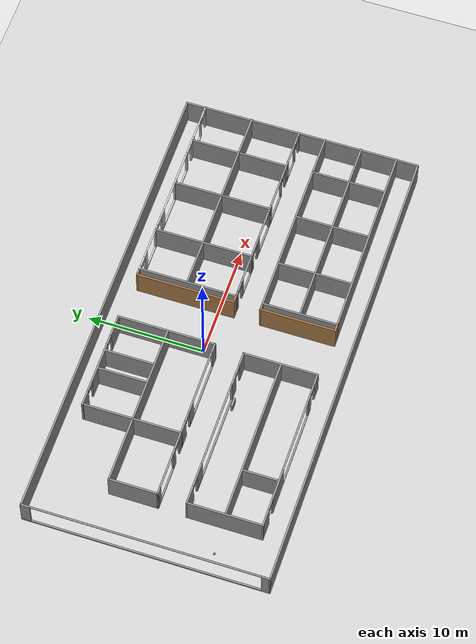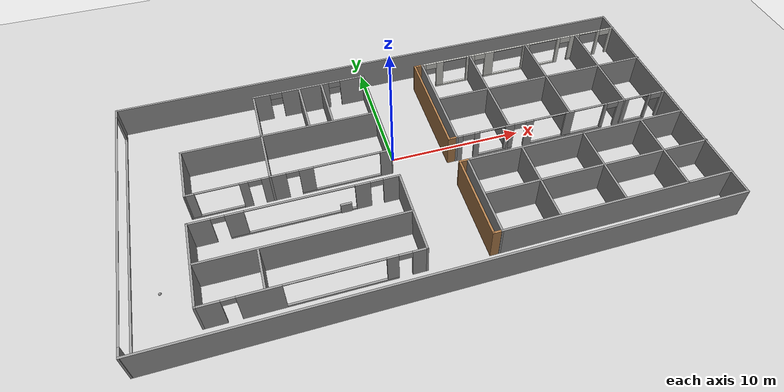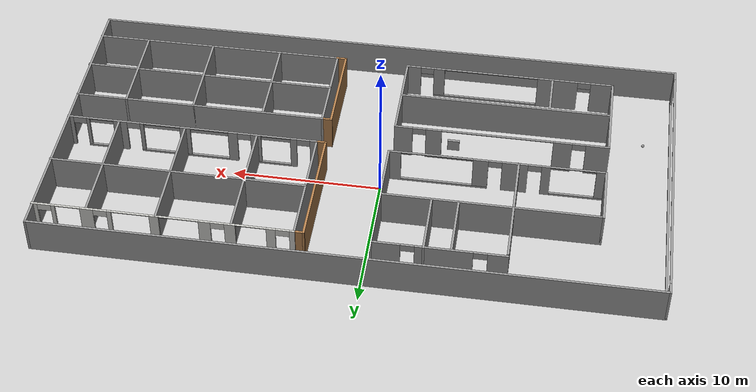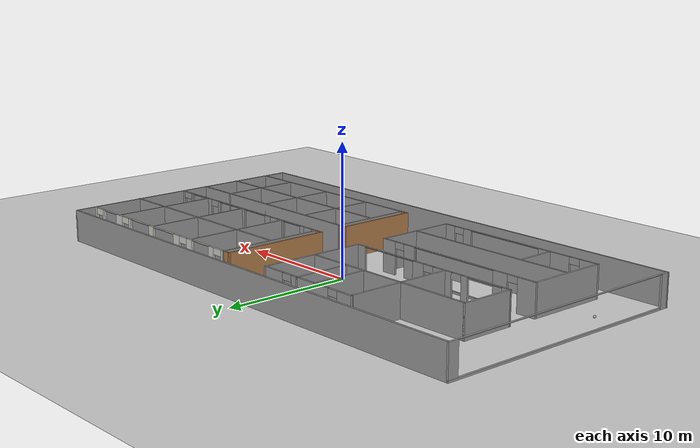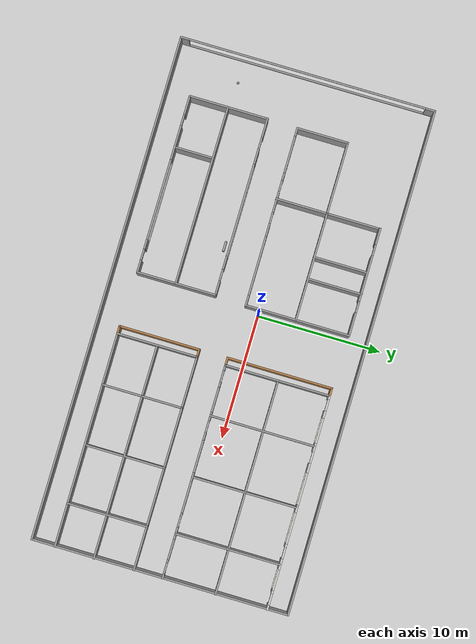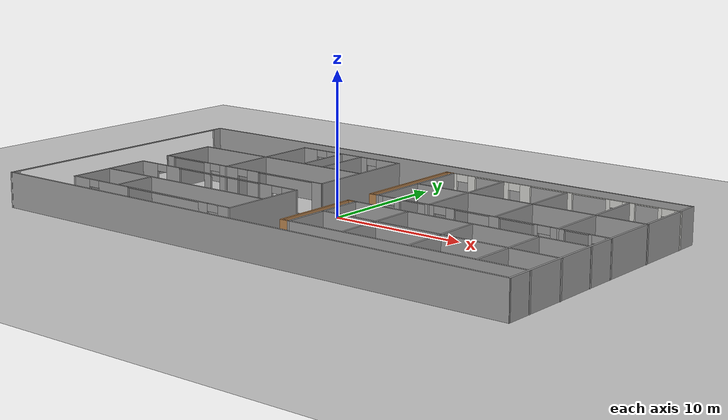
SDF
<sdf version="1.7">
 <world name="default">
  <plugin name="hello" filename="libhello.so"/>
  <light name="sun" type="directional">
   <pose>0 0 10 0 -0 0</pose>
   <diffuse>0.8 0.8 0.8 1</diffuse>
   <specular>0.2 0.2 0.2 1</specular>
   <attenuation>
    <range>1000</range>
    <constant>0.9</constant>
    <linear>0.01</linear>
    <quadratic>0.001</quadratic>
   </attenuation>
   <direction>-0.5 0.1 -0.9</direction>
   <spot><inner_angle>0</inner_angle><outer_angle>0</outer_angle><falloff>0</falloff></spot>
  </light>
  <model name="ground_plane">
   <static>1</static>
   <link name="link">
    <collision name="collision">
     <geometry><plane><normal>0 0 1</normal><size>100 100</size></plane></geometry>
     <surface>
      <contact><collide_bitmask>65535</collide_bitmask></contact>
      <friction><ode><mu>100</mu><mu2>50</mu2></ode></friction>
     </surface>
    </collision>
    <visual name="visual">
     <cast_shadows>0</cast_shadows>
     <geometry><plane><normal>0 0 1</normal><size>100 100</size></plane></geometry>
     <material>
      <script><uri>file://media/materials/scripts/gazebo.material</uri><name>Gazebo/Grey</name></script>
     </material>
    </visual>
   </link>
  </model>
  <gravity>0 0 -9.8</gravity>
  <magnetic_field>6e-06 2.3e-05 -4.2e-05</magnetic_field>
  <atmosphere type="adiabatic"/>
  <physics type="ode">
   <max_step_size>0.001</max_step_size>
   <real_time_factor>1</real_time_factor>
   <real_time_update_rate>1000</real_time_update_rate>
  </physics>
  <scene><ambient>0.4 0.4 0.4 1</ambient><background>0.7 0.7 0.7 1</background><shadows>1</shadows></scene>
  <spherical_coordinates>
   <surface_model>EARTH_WGS84</surface_model>
   <latitude_deg>0</latitude_deg>
   <longitude_deg>0</longitude_deg>
   <elevation>0</elevation>
   <heading_deg>0</heading_deg>
  </spherical_coordinates>
  <model name="SLC_B1">
   <pose>1.2539 -1.59654 0 0 -0 0</pose>
   <link name="Wall_10">
    <pose>-20.3724 4.3e-05 0 0 -0 1.5708</pose>
    <visual name="Wall_10_Visual_0">
     <pose>-10.0243 0 1.25 0 -0 0</pose>
     <geometry><box><size>0.747884 0.15 2.5</size></box></geometry>
     <material>
      <script><uri>file://media/materials/scripts/gazebo.material</uri><name>Gazebo/Grey</name></script>
      <ambient>0.533333 0.541176 0.521569 1</ambient>
     </material>
     <meta><layer>0</layer></meta>
    </visual>
    <collision name="Wall_10_Collision_0">
     <geometry><box><size>0.747884 0.15 2.5</size></box></geometry>
     <pose>-10.0243 0 1.25 0 -0 0</pose>
    </collision>
    <visual name="Wall_10_Visual_1">
     <pose>0.373942 0 0.075 0 -0 0</pose>
     <geometry><box><size>20.0486 0.15 0.15</size></box></geometry>
     <material>
      <script><uri>file://media/materials/scripts/gazebo.material</uri><name>Gazebo/Grey</name></script>
      <ambient>0.533333 0.541176 0.521569 1</ambient>
     </material>
     <meta><layer>0</layer></meta>
    </visual>
    <collision name="Wall_10_Collision_1">
     <geometry><box><size>20.0486 0.15 0.15</size></box></geometry>
     <pose>0.373942 0 0.075 0 -0 0</pose>
    </collision>
    <visual name="Wall_10_Visual_2">
     <pose>9.98544 0 1.325 0 -0 0</pose>
     <geometry><box><size>0.82564 0.15 2.35</size></box></geometry>
     <material>
      <script><uri>file://media/materials/scripts/gazebo.material</uri><name>Gazebo/Grey</name></script>
      <ambient>0.533333 0.541176 0.521569 1</ambient>
     </material>
     <meta><layer>0</layer></meta>
    </visual>
    <collision name="Wall_10_Collision_2">
     <geometry><box><size>0.82564 0.15 2.35</size></box></geometry>
     <pose>9.98544 0 1.325 0 -0 0</pose>
    </collision>
    <visual name="Wall_10_Visual_3">
     <pose>-0.038878 0 2.475 0 -0 0</pose>
     <geometry><box><size>19.223 0.15 0.05</size></box></geometry>
     <material>
      <script><uri>file://media/materials/scripts/gazebo.material</uri><name>Gazebo/Grey</name></script>
      <ambient>0.533333 0.541176 0.521569 1</ambient>
     </material>
     <meta><layer>0</layer></meta>
    </visual>
    <collision name="Wall_10_Collision_3">
     <geometry><box><size>19.223 0.15 0.05</size></box></geometry>
     <pose>-0.038878 0 2.475 0 -0 0</pose>
    </collision>
   </link>
   <link name="Wall_14">
    <pose>11.8092 8.67131 0 0 -0 3.14159</pose>
    <visual name="Wall_14_Visual_0">
     <pose>-8.41077 0 1.25 0 -0 0</pose>
     <geometry><box><size>0.42846 0.15 2.5</size></box></geometry>
     <material>
      <script><uri>file://media/materials/scripts/gazebo.material</uri><name>Gazebo/CeilingTiled</name></script>
      <ambient>0.533333 0.541176 0.521569 1</ambient>
     </material>
     <meta><layer>0</layer></meta>
    </visual>
    <collision name="Wall_14_Collision_0">
     <geometry><box><size>0.42846 0.15 2.5</size></box></geometry>
     <pose>-8.41077 0 1.25 0 -0 0</pose>
    </collision>
    <visual name="Wall_14_Visual_1">
     <pose>-7.17073 0 1.25 0 -0 0</pose>
     <geometry><box><size>0.25162 0.15 2.5</size></box></geometry>
     <material>
      <script><uri>file://media/materials/scripts/gazebo.material</uri><name>Gazebo/CeilingTiled</name></script>
      <ambient>0.533333 0.541176 0.521569 1</ambient>
     </material>
     <meta><layer>0</layer></meta>
    </visual>
    <collision name="Wall_14_Collision_1">
     <geometry><box><size>0.25162 0.15 2.5</size></box></geometry>
     <pose>-7.17073 0 1.25 0 -0 0</pose>
    </collision>
    <visual name="Wall_14_Visual_2">
     <pose>-3.47416 0 1.25 0 -0 0</pose>
     <geometry><box><size>0.289232 0.15 2.5</size></box></geometry>
     <material>
      <script><uri>file://media/materials/scripts/gazebo.material</uri><name>Gazebo/CeilingTiled</name></script>
      <ambient>0.533333 0.541176 0.521569 1</ambient>
     </material>
     <meta><layer>0</layer></meta>
    </visual>
    <collision name="Wall_14_Collision_2">
     <geometry><box><size>0.289232 0.15 2.5</size></box></geometry>
     <pose>-3.47416 0 1.25 0 -0 0</pose>
    </collision>
    <visual name="Wall_14_Visual_3">
     <pose>4.41694 0 1.25 0 -0 0</pose>
     <geometry><box><size>0.712712 0.15 2.5</size></box></geometry>
     <material>
      <script><uri>file://media/materials/scripts/gazebo.material</uri><name>Gazebo/CeilingTiled</name></script>
      <ambient>0.533333 0.541176 0.521569 1</ambient>
     </material>
     <meta><layer>0</layer></meta>
    </visual>
    <collision name="Wall_14_Collision_3">
     <geometry><box><size>0.712712 0.15 2.5</size></box></geometry>
     <pose>4.41694 0 1.25 0 -0 0</pose>
    </collision>
    <visual name="Wall_14_Visual_4">
     <pose>8.44768 0 1.25 0 -0 0</pose>
     <geometry><box><size>0.354641 0.15 2.5</size></box></geometry>
     <material>
      <script><uri>file://media/materials/scripts/gazebo.material</uri><name>Gazebo/CeilingTiled</name></script>
      <ambient>0.533333 0.541176 0.521569 1</ambient>
     </material>
     <meta><layer>0</layer></meta>
    </visual>
    <collision name="Wall_14_Collision_4">
     <geometry><box><size>0.354641 0.15 2.5</size></box></geometry>
     <pose>8.44768 0 1.25 0 -0 0</pose>
    </collision>
    <visual name="Wall_14_Visual_5">
     <pose>-5.78185 0 0.075 0 -0 0</pose>
     <geometry><box><size>2.52615 0.15 0.15</size></box></geometry>
     <material>
      <script><uri>file://media/materials/scripts/gazebo.material</uri><name>Gazebo/CeilingTiled</name></script>
      <ambient>0.533333 0.541176 0.521569 1</ambient>
     </material>
     <meta><layer>0</layer></meta>
    </visual>
    <collision name="Wall_14_Collision_5">
     <geometry><box><size>2.52615 0.15 0.15</size></box></geometry>
     <pose>-5.78185 0 0.075 0 -0 0</pose>
    </collision>
    <visual name="Wall_14_Visual_6">
     <pose>-0.084477 0 0.075 0 -0 0</pose>
     <geometry><box><size>6.49013 0.15 0.15</size></box></geometry>
     <material>
      <script><uri>file://media/materials/scripts/gazebo.material</uri><name>Gazebo/CeilingTiled</name></script>
      <ambient>0.533333 0.541176 0.521569 1</ambient>
     </material>
     <meta><layer>0</layer></meta>
    </visual>
    <collision name="Wall_14_Collision_6">
     <geometry><box><size>6.49013 0.15 0.15</size></box></geometry>
     <pose>-0.084477 0 0.075 0 -0 0</pose>
    </collision>
    <visual name="Wall_14_Visual_7">
     <pose>6.07183 0 0.075 0 -0 0</pose>
     <geometry><box><size>2.59706 0.15 0.15</size></box></geometry>
     <material>
      <script><uri>file://media/materials/scripts/gazebo.material</uri><name>Gazebo/CeilingTiled</name></script>
      <ambient>0.533333 0.541176 0.521569 1</ambient>
     </material>
     <meta><layer>0</layer></meta>
    </visual>
    <collision name="Wall_14_Collision_7">
     <geometry><box><size>2.59706 0.15 0.15</size></box></geometry>
     <pose>6.07183 0 0.075 0 -0 0</pose>
    </collision>
    <visual name="Wall_14_Visual_8">
     <pose>-4.95685 0 1.325 0 -0 0</pose>
     <geometry><box><size>0.876146 0.15 2.35</size></box></geometry>
     <material>
      <script><uri>file://media/materials/scripts/gazebo.material</uri><name>Gazebo/CeilingTiled</name></script>
      <ambient>0.533333 0.541176 0.521569 1</ambient>
     </material>
     <meta><layer>0</layer></meta>
    </visual>
    <collision name="Wall_14_Collision_8">
     <geometry><box><size>0.876146 0.15 2.35</size></box></geometry>
     <pose>-4.95685 0 1.325 0 -0 0</pose>
    </collision>
    <visual name="Wall_14_Visual_9">
     <pose>-4.95685 0 1.325 0 -0 0</pose>
     <geometry><box><size>0.876146 0.15 2.35</size></box></geometry>
     <material>
      <script><uri>file://media/materials/scripts/gazebo.material</uri><name>Gazebo/CeilingTiled</name></script>
      <ambient>0.533333 0.541176 0.521569 1</ambient>
     </material>
     <meta><layer>0</layer></meta>
    </visual>
    <collision name="Wall_14_Collision_9">
     <geometry><box><size>0.876146 0.15 2.35</size></box></geometry>
     <pose>-4.95685 0 1.325 0 -0 0</pose>
    </collision>
    <visual name="Wall_14_Visual_10">
     <pose>-0.525878 0 1.325 0 -0 0</pose>
     <geometry><box><size>0.607328 0.15 2.35</size></box></geometry>
     <material>
      <script><uri>file://media/materials/scripts/gazebo.material</uri><name>Gazebo/CeilingTiled</name></script>
      <ambient>0.533333 0.541176 0.521569 1</ambient>
     </material>
     <meta><layer>0</layer></meta>
    </visual>
    <collision name="Wall_14_Collision_10">
     <geometry><box><size>0.607328 0.15 2.35</size></box></geometry>
     <pose>-0.525878 0 1.325 0 -0 0</pose>
    </collision>
    <visual name="Wall_14_Visual_11">
     <pose>2.76919 0 1.325 0 -0 0</pose>
     <geometry><box><size>0.782801 0.15 2.35</size></box></geometry>
     <material>
      <script><uri>file://media/materials/scripts/gazebo.material</uri><name>Gazebo/CeilingTiled</name></script>
      <ambient>0.533333 0.541176 0.521569 1</ambient>
     </material>
     <meta><layer>0</layer></meta>
    </visual>
    <collision name="Wall_14_Collision_11">
     <geometry><box><size>0.782801 0.15 2.35</size></box></geometry>
     <pose>2.76919 0 1.325 0 -0 0</pose>
    </collision>
    <visual name="Wall_14_Visual_12">
     <pose>2.76919 0 1.325 0 -0 0</pose>
     <geometry><box><size>0.782801 0.15 2.35</size></box></geometry>
     <material>
      <script><uri>file://media/materials/scripts/gazebo.material</uri><name>Gazebo/CeilingTiled</name></script>
      <ambient>0.533333 0.541176 0.521569 1</ambient>
     </material>
     <meta><layer>0</layer></meta>
    </visual>
    <collision name="Wall_14_Collision_12">
     <geometry><box><size>0.782801 0.15 2.35</size></box></geometry>
     <pose>2.76919 0 1.325 0 -0 0</pose>
    </collision>
    <visual name="Wall_14_Visual_13">
     <pose>7.07183 0 1.325 0 -0 0</pose>
     <geometry><box><size>0.597059 0.15 2.35</size></box></geometry>
     <material>
      <script><uri>file://media/materials/scripts/gazebo.material</uri><name>Gazebo/CeilingTiled</name></script>
      <ambient>0.533333 0.541176 0.521569 1</ambient>
     </material>
     <meta><layer>0</layer></meta>
    </visual>
    <collision name="Wall_14_Collision_13">
     <geometry><box><size>0.597059 0.15 2.35</size></box></geometry>
     <pose>7.07183 0 1.325 0 -0 0</pose>
    </collision>
    <visual name="Wall_14_Visual_14">
     <pose>-7.74654 0 2.25 0 -0 0</pose>
     <geometry><box><size>0.9 0.15 0.5</size></box></geometry>
     <material>
      <script><uri>file://media/materials/scripts/gazebo.material</uri><name>Gazebo/CeilingTiled</name></script>
      <ambient>0.533333 0.541176 0.521569 1</ambient>
     </material>
     <meta><layer>0</layer></meta>
    </visual>
    <collision name="Wall_14_Collision_14">
     <geometry><box><size>0.9 0.15 0.5</size></box></geometry>
     <pose>-7.74654 0 2.25 0 -0 0</pose>
    </collision>
    <visual name="Wall_14_Visual_15">
     <pose>-4.06877 0 2.25 0 -0 0</pose>
     <geometry><box><size>0.9 0.15 0.5</size></box></geometry>
     <material>
      <script><uri>file://media/materials/scripts/gazebo.material</uri><name>Gazebo/CeilingTiled</name></script>
      <ambient>0.533333 0.541176 0.521569 1</ambient>
     </material>
     <meta><layer>0</layer></meta>
    </visual>
    <collision name="Wall_14_Collision_15">
     <geometry><box><size>0.9 0.15 0.5</size></box></geometry>
     <pose>-4.06877 0 2.25 0 -0 0</pose>
    </collision>
    <visual name="Wall_14_Visual_16">
     <pose>-4.06877 0 2.25 0 -0 0</pose>
     <geometry><box><size>0.9 0.15 0.5</size></box></geometry>
     <material>
      <script><uri>file://media/materials/scripts/gazebo.material</uri><name>Gazebo/CeilingTiled</name></script>
      <ambient>0.533333 0.541176 0.521569 1</ambient>
     </material>
     <meta><layer>0</layer></meta>
    </visual>
    <collision name="Wall_14_Collision_16">
     <geometry><box><size>0.9 0.15 0.5</size></box></geometry>
     <pose>-4.06877 0 2.25 0 -0 0</pose>
    </collision>
    <visual name="Wall_14_Visual_17">
     <pose>3.61059 0 2.25 0 -0 0</pose>
     <geometry><box><size>0.9 0.15 0.5</size></box></geometry>
     <material>
      <script><uri>file://media/materials/scripts/gazebo.material</uri><name>Gazebo/CeilingTiled</name></script>
      <ambient>0.533333 0.541176 0.521569 1</ambient>
     </material>
     <meta><layer>0</layer></meta>
    </visual>
    <collision name="Wall_14_Collision_17">
     <geometry><box><size>0.9 0.15 0.5</size></box></geometry>
     <pose>3.61059 0 2.25 0 -0 0</pose>
    </collision>
    <visual name="Wall_14_Visual_18">
     <pose>3.61059 0 2.25 0 -0 0</pose>
     <geometry><box><size>0.9 0.15 0.5</size></box></geometry>
     <material>
      <script><uri>file://media/materials/scripts/gazebo.material</uri><name>Gazebo/CeilingTiled</name></script>
      <ambient>0.533333 0.541176 0.521569 1</ambient>
     </material>
     <meta><layer>0</layer></meta>
    </visual>
    <collision name="Wall_14_Collision_18">
     <geometry><box><size>0.9 0.15 0.5</size></box></geometry>
     <pose>3.61059 0 2.25 0 -0 0</pose>
    </collision>
    <visual name="Wall_14_Visual_19">
     <pose>7.82036 0 2.25 0 -0 0</pose>
     <geometry><box><size>0.9 0.15 0.5</size></box></geometry>
     <material>
      <script><uri>file://media/materials/scripts/gazebo.material</uri><name>Gazebo/CeilingTiled</name></script>
      <ambient>0.533333 0.541176 0.521569 1</ambient>
     </material>
     <meta><layer>0</layer></meta>
    </visual>
    <collision name="Wall_14_Collision_19">
     <geometry><box><size>0.9 0.15 0.5</size></box></geometry>
     <pose>7.82036 0 2.25 0 -0 0</pose>
    </collision>
    <visual name="Wall_14_Visual_20">
     <pose>-6.21992 0 2.475 0 -0 0</pose>
     <geometry><box><size>1.65 0.15 0.05</size></box></geometry>
     <material>
      <script><uri>file://media/materials/scripts/gazebo.material</uri><name>Gazebo/CeilingTiled</name></script>
      <ambient>0.533333 0.541176 0.521569 1</ambient>
     </material>
     <meta><layer>0</layer></meta>
    </visual>
    <collision name="Wall_14_Collision_20">
     <geometry><box><size>1.65 0.15 0.05</size></box></geometry>
     <pose>-6.21992 0 2.475 0 -0 0</pose>
    </collision>
    <visual name="Wall_14_Visual_21">
     <pose>-2.07954 0 2.475 0 -0 0</pose>
     <geometry><box><size>2.5 0.15 0.05</size></box></geometry>
     <material>
      <script><uri>file://media/materials/scripts/gazebo.material</uri><name>Gazebo/CeilingTiled</name></script>
      <ambient>0.533333 0.541176 0.521569 1</ambient>
     </material>
     <meta><layer>0</layer></meta>
    </visual>
    <collision name="Wall_14_Collision_21">
     <geometry><box><size>2.5 0.15 0.05</size></box></geometry>
     <pose>-2.07954 0 2.475 0 -0 0</pose>
    </collision>
    <visual name="Wall_14_Visual_22">
     <pose>5.7733 0 2.475 0 -0 0</pose>
     <geometry><box><size>2 0.15 0.05</size></box></geometry>
     <material>
      <script><uri>file://media/materials/scripts/gazebo.material</uri><name>Gazebo/CeilingTiled</name></script>
      <ambient>0.533333 0.541176 0.521569 1</ambient>
     </material>
     <meta><layer>0</layer></meta>
    </visual>
    <collision name="Wall_14_Collision_22">
     <geometry><box><size>2 0.15 0.05</size></box></geometry>
     <pose>5.7733 0 2.475 0 -0 0</pose>
    </collision>
    <visual name="Wall_14_Visual_23">
     <pose>1.07779 0 2.475 0 -0 0</pose>
     <geometry><box><size>2.6 0.15 0.05</size></box></geometry>
     <material>
      <script><uri>file://media/materials/scripts/gazebo.material</uri><name>Gazebo/CeilingTiled</name></script>
      <ambient>0.533333 0.541176 0.521569 1</ambient>
     </material>
     <meta><layer>0</layer></meta>
    </visual>
    <collision name="Wall_14_Collision_23">
     <geometry><box><size>2.6 0.15 0.05</size></box></geometry>
     <pose>1.07779 0 2.475 0 -0 0</pose>
    </collision>
   </link>
   <link name="Wall_15">
    <collision name="Wall_15_Collision">
     <geometry><box><size>8.56942 0.15 2.5</size></box></geometry>
     <pose>0 0 1.25 0 -0 0</pose>
    </collision>
    <visual name="Wall_15_Visual">
     <pose>0 0 1.25 0 -0 0</pose>
     <geometry><box><size>8.56942 0.15 2.5</size></box></geometry>
     <material>
      <script><uri>file://media/materials/scripts/gazebo.material</uri><name>Gazebo/Grey</name></script>
      <ambient>0.533333 0.541176 0.521569 1</ambient>
     </material>
     <meta><layer>0</layer></meta>
    </visual>
    <pose>3.23606 4.46162 0 0 -0 -1.5708</pose>
   </link>
   <link name="Wall_16">
    <pose>11.7861 0.25192 0 0 -0 0</pose>
    <visual name="Wall_16_Visual_0">
     <pose>-8.35766 0 1.25 0 -0 0</pose>
     <geometry><box><size>0.534678 0.15 2.5</size></box></geometry>
     <material>
      <script><uri>file://media/materials/scripts/gazebo.material</uri><name>Gazebo/Grey</name></script>
      <ambient>0.533333 0.541176 0.521569 1</ambient>
     </material>
     <meta><layer>0</layer></meta>
    </visual>
    <collision name="Wall_16_Collision_0">
     <geometry><box><size>0.534678 0.15 2.5</size></box></geometry>
     <pose>-8.35766 0 1.25 0 -0 0</pose>
    </collision>
    <visual name="Wall_16_Visual_1">
     <pose>-6.97321 0 1.25 0 -0 0</pose>
     <geometry><box><size>0.434218 0.15 2.5</size></box></geometry>
     <material>
      <script><uri>file://media/materials/scripts/gazebo.material</uri><name>Gazebo/Grey</name></script>
      <ambient>0.533333 0.541176 0.521569 1</ambient>
     </material>
     <meta><layer>0</layer></meta>
    </visual>
    <collision name="Wall_16_Collision_1">
     <geometry><box><size>0.434218 0.15 2.5</size></box></geometry>
     <pose>-6.97321 0 1.25 0 -0 0</pose>
    </collision>
    <visual name="Wall_16_Visual_2">
     <pose>-2.81975 0 1.25 0 -0 0</pose>
     <geometry><box><size>0.645982 0.15 2.5</size></box></geometry>
     <material>
      <script><uri>file://media/materials/scripts/gazebo.material</uri><name>Gazebo/Grey</name></script>
      <ambient>0.533333 0.541176 0.521569 1</ambient>
     </material>
     <meta><layer>0</layer></meta>
    </visual>
    <collision name="Wall_16_Collision_2">
     <geometry><box><size>0.645982 0.15 2.5</size></box></geometry>
     <pose>-2.81975 0 1.25 0 -0 0</pose>
    </collision>
    <visual name="Wall_16_Visual_3">
     <pose>4.96072 0 1.25 0 -0 0</pose>
     <geometry><box><size>0.947074 0.15 2.5</size></box></geometry>
     <material>
      <script><uri>file://media/materials/scripts/gazebo.material</uri><name>Gazebo/Grey</name></script>
      <ambient>0.533333 0.541176 0.521569 1</ambient>
     </material>
     <meta><layer>0</layer></meta>
    </visual>
    <collision name="Wall_16_Collision_3">
     <geometry><box><size>0.947074 0.15 2.5</size></box></geometry>
     <pose>4.96072 0 1.25 0 -0 0</pose>
    </collision>
    <visual name="Wall_16_Visual_4">
     <pose>8.41705 0 1.25 0 -0 0</pose>
     <geometry><box><size>0.415906 0.15 2.5</size></box></geometry>
     <material>
      <script><uri>file://media/materials/scripts/gazebo.material</uri><name>Gazebo/Grey</name></script>
      <ambient>0.533333 0.541176 0.521569 1</ambient>
     </material>
     <meta><layer>0</layer></meta>
    </visual>
    <collision name="Wall_16_Collision_4">
     <geometry><box><size>0.415906 0.15 2.5</size></box></geometry>
     <pose>8.41705 0 1.25 0 -0 0</pose>
    </collision>
    <visual name="Wall_16_Visual_5">
     <pose>-5.39942 0 0.075 0 -0 0</pose>
     <geometry><box><size>2.71336 0.15 0.15</size></box></geometry>
     <material>
      <script><uri>file://media/materials/scripts/gazebo.material</uri><name>Gazebo/Grey</name></script>
      <ambient>0.533333 0.541176 0.521569 1</ambient>
     </material>
     <meta><layer>0</layer></meta>
    </visual>
    <collision name="Wall_16_Collision_5">
     <geometry><box><size>2.71336 0.15 0.15</size></box></geometry>
     <pose>-5.39942 0 0.075 0 -0 0</pose>
    </collision>
    <visual name="Wall_16_Visual_6">
     <pose>0.54521 0 0.075 0 -0 0</pose>
     <geometry><box><size>6.08394 0.15 0.15</size></box></geometry>
     <material>
      <script><uri>file://media/materials/scripts/gazebo.material</uri><name>Gazebo/Grey</name></script>
      <ambient>0.533333 0.541176 0.521569 1</ambient>
     </material>
     <meta><layer>0</layer></meta>
    </visual>
    <collision name="Wall_16_Collision_6">
     <geometry><box><size>6.08394 0.15 0.15</size></box></geometry>
     <pose>0.54521 0 0.075 0 -0 0</pose>
    </collision>
    <visual name="Wall_16_Visual_7">
     <pose>6.37167 0 0.075 0 -0 0</pose>
     <geometry><box><size>1.87484 0.15 0.15</size></box></geometry>
     <material>
      <script><uri>file://media/materials/scripts/gazebo.material</uri><name>Gazebo/Grey</name></script>
      <ambient>0.533333 0.541176 0.521569 1</ambient>
     </material>
     <meta><layer>0</layer></meta>
    </visual>
    <collision name="Wall_16_Collision_7">
     <geometry><box><size>1.87484 0.15 0.15</size></box></geometry>
     <pose>6.37167 0 0.075 0 -0 0</pose>
    </collision>
    <visual name="Wall_16_Visual_8">
     <pose>-4.39942 0 1.325 0 -0 0</pose>
     <geometry><box><size>0.713362 0.15 2.35</size></box></geometry>
     <material>
      <script><uri>file://media/materials/scripts/gazebo.material</uri><name>Gazebo/Grey</name></script>
      <ambient>0.533333 0.541176 0.521569 1</ambient>
     </material>
     <meta><layer>0</layer></meta>
    </visual>
    <collision name="Wall_16_Collision_8">
     <geometry><box><size>0.713362 0.15 2.35</size></box></geometry>
     <pose>-4.39942 0 1.325 0 -0 0</pose>
    </collision>
    <visual name="Wall_16_Visual_9">
     <pose>-4.39942 0 1.325 0 -0 0</pose>
     <geometry><box><size>0.713362 0.15 2.35</size></box></geometry>
     <material>
      <script><uri>file://media/materials/scripts/gazebo.material</uri><name>Gazebo/Grey</name></script>
      <ambient>0.533333 0.541176 0.521569 1</ambient>
     </material>
     <meta><layer>0</layer></meta>
    </visual>
    <collision name="Wall_16_Collision_9">
     <geometry><box><size>0.713362 0.15 2.35</size></box></geometry>
     <pose>-4.39942 0 1.325 0 -0 0</pose>
    </collision>
    <visual name="Wall_16_Visual_10">
     <pose>0.468208 0 1.325 0 -0 0</pose>
     <geometry><box><size>0.729936 0.15 2.35</size></box></geometry>
     <material>
      <script><uri>file://media/materials/scripts/gazebo.material</uri><name>Gazebo/Grey</name></script>
      <ambient>0.533333 0.541176 0.521569 1</ambient>
     </material>
     <meta><layer>0</layer></meta>
    </visual>
    <collision name="Wall_16_Collision_10">
     <geometry><box><size>0.729936 0.15 2.35</size></box></geometry>
     <pose>0.468208 0 1.325 0 -0 0</pose>
    </collision>
    <visual name="Wall_16_Visual_11">
     <pose>3.46018 0 1.325 0 -0 0</pose>
     <geometry><box><size>0.254004 0.15 2.35</size></box></geometry>
     <material>
      <script><uri>file://media/materials/scripts/gazebo.material</uri><name>Gazebo/Grey</name></script>
      <ambient>0.533333 0.541176 0.521569 1</ambient>
     </material>
     <meta><layer>0</layer></meta>
    </visual>
    <collision name="Wall_16_Collision_11">
     <geometry><box><size>0.254004 0.15 2.35</size></box></geometry>
     <pose>3.46018 0 1.325 0 -0 0</pose>
    </collision>
    <visual name="Wall_16_Visual_12">
     <pose>3.46018 0 1.325 0 -0 0</pose>
     <geometry><box><size>0.254004 0.15 2.35</size></box></geometry>
     <material>
      <script><uri>file://media/materials/scripts/gazebo.material</uri><name>Gazebo/Grey</name></script>
      <ambient>0.533333 0.541176 0.521569 1</ambient>
     </material>
     <meta><layer>0</layer></meta>
    </visual>
    <collision name="Wall_16_Collision_12">
     <geometry><box><size>0.254004 0.15 2.35</size></box></geometry>
     <pose>3.46018 0 1.325 0 -0 0</pose>
    </collision>
    <visual name="Wall_16_Visual_13">
     <pose>7.20017 0 1.325 0 -0 0</pose>
     <geometry><box><size>0.217839 0.15 2.35</size></box></geometry>
     <material>
      <script><uri>file://media/materials/scripts/gazebo.material</uri><name>Gazebo/Grey</name></script>
      <ambient>0.533333 0.541176 0.521569 1</ambient>
     </material>
     <meta><layer>0</layer></meta>
    </visual>
    <collision name="Wall_16_Collision_13">
     <geometry><box><size>0.217839 0.15 2.35</size></box></geometry>
     <pose>7.20017 0 1.325 0 -0 0</pose>
    </collision>
    <visual name="Wall_16_Visual_14">
     <pose>-7.64032 0 2.25 0 -0 0</pose>
     <geometry><box><size>0.9 0.15 0.5</size></box></geometry>
     <material>
      <script><uri>file://media/materials/scripts/gazebo.material</uri><name>Gazebo/Grey</name></script>
      <ambient>0.533333 0.541176 0.521569 1</ambient>
     </material>
     <meta><layer>0</layer></meta>
    </visual>
    <collision name="Wall_16_Collision_14">
     <geometry><box><size>0.9 0.15 0.5</size></box></geometry>
     <pose>-7.64032 0 2.25 0 -0 0</pose>
    </collision>
    <visual name="Wall_16_Visual_15">
     <pose>-3.59274 0 2.25 0 -0 0</pose>
     <geometry><box><size>0.9 0.15 0.5</size></box></geometry>
     <material>
      <script><uri>file://media/materials/scripts/gazebo.material</uri><name>Gazebo/Grey</name></script>
      <ambient>0.533333 0.541176 0.521569 1</ambient>
     </material>
     <meta><layer>0</layer></meta>
    </visual>
    <collision name="Wall_16_Collision_15">
     <geometry><box><size>0.9 0.15 0.5</size></box></geometry>
     <pose>-3.59274 0 2.25 0 -0 0</pose>
    </collision>
    <visual name="Wall_16_Visual_16">
     <pose>-3.59274 0 2.25 0 -0 0</pose>
     <geometry><box><size>0.9 0.15 0.5</size></box></geometry>
     <material>
      <script><uri>file://media/materials/scripts/gazebo.material</uri><name>Gazebo/Grey</name></script>
      <ambient>0.533333 0.541176 0.521569 1</ambient>
     </material>
     <meta><layer>0</layer></meta>
    </visual>
    <collision name="Wall_16_Collision_16">
     <geometry><box><size>0.9 0.15 0.5</size></box></geometry>
     <pose>-3.59274 0 2.25 0 -0 0</pose>
    </collision>
    <visual name="Wall_16_Visual_17">
     <pose>4.03718 0 2.25 0 -0 0</pose>
     <geometry><box><size>0.9 0.15 0.5</size></box></geometry>
     <material>
      <script><uri>file://media/materials/scripts/gazebo.material</uri><name>Gazebo/Grey</name></script>
      <ambient>0.533333 0.541176 0.521569 1</ambient>
     </material>
     <meta><layer>0</layer></meta>
    </visual>
    <collision name="Wall_16_Collision_17">
     <geometry><box><size>0.9 0.15 0.5</size></box></geometry>
     <pose>4.03718 0 2.25 0 -0 0</pose>
    </collision>
    <visual name="Wall_16_Visual_18">
     <pose>4.03718 0 2.25 0 -0 0</pose>
     <geometry><box><size>0.9 0.15 0.5</size></box></geometry>
     <material>
      <script><uri>file://media/materials/scripts/gazebo.material</uri><name>Gazebo/Grey</name></script>
      <ambient>0.533333 0.541176 0.521569 1</ambient>
     </material>
     <meta><layer>0</layer></meta>
    </visual>
    <collision name="Wall_16_Collision_18">
     <geometry><box><size>0.9 0.15 0.5</size></box></geometry>
     <pose>4.03718 0 2.25 0 -0 0</pose>
    </collision>
    <visual name="Wall_16_Visual_19">
     <pose>7.75909 0 2.25 0 -0 0</pose>
     <geometry><box><size>0.9 0.15 0.5</size></box></geometry>
     <material>
      <script><uri>file://media/materials/scripts/gazebo.material</uri><name>Gazebo/Grey</name></script>
      <ambient>0.533333 0.541176 0.521569 1</ambient>
     </material>
     <meta><layer>0</layer></meta>
    </visual>
    <collision name="Wall_16_Collision_19">
     <geometry><box><size>0.9 0.15 0.5</size></box></geometry>
     <pose>7.75909 0 2.25 0 -0 0</pose>
    </collision>
    <visual name="Wall_16_Visual_20">
     <pose>-5.7561 0 2.475 0 -0 0</pose>
     <geometry><box><size>2 0.15 0.05</size></box></geometry>
     <material>
      <script><uri>file://media/materials/scripts/gazebo.material</uri><name>Gazebo/Grey</name></script>
      <ambient>0.533333 0.541176 0.521569 1</ambient>
     </material>
     <meta><layer>0</layer></meta>
    </visual>
    <collision name="Wall_16_Collision_20">
     <geometry><box><size>2 0.15 0.05</size></box></geometry>
     <pose>-5.7561 0 2.475 0 -0 0</pose>
    </collision>
    <visual name="Wall_16_Visual_21">
     <pose>-1.19676 0 2.475 0 -0 0</pose>
     <geometry><box><size>2.6 0.15 0.05</size></box></geometry>
     <material>
      <script><uri>file://media/materials/scripts/gazebo.material</uri><name>Gazebo/Grey</name></script>
      <ambient>0.533333 0.541176 0.521569 1</ambient>
     </material>
     <meta><layer>0</layer></meta>
    </visual>
    <collision name="Wall_16_Collision_21">
     <geometry><box><size>2.6 0.15 0.05</size></box></geometry>
     <pose>-1.19676 0 2.475 0 -0 0</pose>
    </collision>
    <visual name="Wall_16_Visual_22">
     <pose>6.26276 0 2.475 0 -0 0</pose>
     <geometry><box><size>1.657 0.15 0.05</size></box></geometry>
     <material>
      <script><uri>file://media/materials/scripts/gazebo.material</uri><name>Gazebo/Grey</name></script>
      <ambient>0.533333 0.541176 0.521569 1</ambient>
     </material>
     <meta><layer>0</layer></meta>
    </visual>
    <collision name="Wall_16_Collision_22">
     <geometry><box><size>1.657 0.15 0.05</size></box></geometry>
     <pose>6.26276 0 2.475 0 -0 0</pose>
    </collision>
    <visual name="Wall_16_Visual_23">
     <pose>2.08318 0 2.475 0 -0 0</pose>
     <geometry><box><size>2.5 0.15 0.05</size></box></geometry>
     <material>
      <script><uri>file://media/materials/scripts/gazebo.material</uri><name>Gazebo/Grey</name></script>
      <ambient>0.533333 0.541176 0.521569 1</ambient>
     </material>
     <meta><layer>0</layer></meta>
    </visual>
    <collision name="Wall_16_Collision_23">
     <geometry><box><size>2.5 0.15 0.05</size></box></geometry>
     <pose>2.08318 0 2.475 0 -0 0</pose>
    </collision>
   </link>
   <link name="Wall_18">
    <collision name="Wall_18_Collision">
     <geometry><box><size>17.25 0.15 2.5</size></box></geometry>
     <pose>0 0 1.25 0 -0 0</pose>
    </collision>
    <visual name="Wall_18_Visual">
     <pose>0 0 1.25 0 -0 0</pose>
     <geometry><box><size>17.25 0.15 2.5</size></box></geometry>
     <material>
      <script><uri>file://media/materials/scripts/gazebo.material</uri><name>Gazebo/Grey</name></script>
      <ambient>0.533333 0.541176 0.521569 1</ambient>
     </material>
     <meta><layer>0</layer></meta>
    </visual>
    <pose>11.8118 4.50781 0 0 -0 0</pose>
   </link>
   <link name="Wall_23">
    <collision name="Wall_23_Collision">
     <geometry><box><size>8.5 0.15 2.5</size></box></geometry>
     <pose>0 0 1.25 0 -0 0</pose>
    </collision>
    <visual name="Wall_23_Visual">
     <pose>0 0 1.25 0 -0 0</pose>
     <geometry><box><size>8.5 0.15 2.5</size></box></geometry>
     <material>
      <script><uri>file://media/materials/scripts/gazebo.material</uri><name>Gazebo/Grey</name></script>
      <ambient>0.533333 0.541176 0.521569 1</ambient>
     </material>
     <meta><layer>0</layer></meta>
    </visual>
    <pose>7.30937 4.42692 0 0 -0 -1.5708</pose>
   </link>
   <link name="Wall_29">
    <collision name="Wall_29_Collision">
     <geometry><box><size>8.5 0.15 2.5</size></box></geometry>
     <pose>0 0 1.25 0 -0 0</pose>
    </collision>
    <visual name="Wall_29_Visual">
     <pose>0 0 1.25 0 -0 0</pose>
     <geometry><box><size>8.5 0.15 2.5</size></box></geometry>
     <material>
      <script><uri>file://media/materials/scripts/gazebo.material</uri><name>Gazebo/Grey</name></script>
      <ambient>0.533333 0.541176 0.521569 1</ambient>
     </material>
     <meta><layer>0</layer></meta>
    </visual>
    <pose>12.2409 4.42692 0 0 -0 -1.5708</pose>
   </link>
   <link name="Wall_33">
    <collision name="Wall_33_Collision">
     <geometry><box><size>8.5 0.15 2.5</size></box></geometry>
     <pose>0 0 1.25 0 -0 0</pose>
    </collision>
    <visual name="Wall_33_Visual">
     <pose>0 0 1.25 0 -0 0</pose>
     <geometry><box><size>8.5 0.15 2.5</size></box></geometry>
     <material>
      <script><uri>file://media/materials/scripts/gazebo.material</uri><name>Gazebo/Grey</name></script>
      <ambient>0.533333 0.541176 0.521569 1</ambient>
     </material>
     <meta><layer>0</layer></meta>
    </visual>
    <pose>16.8002 4.42692 0 0 -0 -1.5708</pose>
   </link>
   <link name="Wall_39">
    <collision name="Wall_39_Collision">
     <geometry><box><size>17.25 0.15 2.5</size></box></geometry>
     <pose>0 0 1.25 0 -0 0</pose>
    </collision>
    <visual name="Wall_39_Visual">
     <pose>0 0 1.25 0 -0 0</pose>
     <geometry><box><size>17.25 0.15 2.5</size></box></geometry>
     <material>
      <script><uri>file://media/materials/scripts/gazebo.material</uri><name>Gazebo/Grey</name></script>
      <ambient>0.533333 0.541176 0.521569 1</ambient>
     </material>
     <meta><layer>0</layer></meta>
    </visual>
    <pose>11.7968 -2.04592 0 0 -0 3.14159</pose>
   </link>
   <link name="Wall_40">
    <collision name="Wall_40_Collision">
     <geometry><box><size>6.57614 0.15 2.5</size></box></geometry>
     <pose>0 0 1.25 0 -0 0</pose>
    </collision>
    <visual name="Wall_40_Visual">
     <pose>0 0 1.25 0 -0 0</pose>
     <geometry><box><size>6.57614 0.15 2.5</size></box></geometry>
     <material>
      <script><uri>file://media/materials/scripts/gazebo.material</uri><name>Gazebo/Grey</name></script>
      <ambient>0.533333 0.541176 0.521569 1</ambient>
     </material>
     <meta><layer>0</layer></meta>
    </visual>
    <pose>3.24677 -5.25874 0 0 -0 -1.5708</pose>
   </link>
   <link name="Wall_41">
    <collision name="Wall_41_Collision">
     <geometry><box><size>17.2502 0.15 2.5</size></box></geometry>
     <pose>0 0 1.25 0 -0 0</pose>
    </collision>
    <visual name="Wall_41_Visual">
     <pose>0 0 1.25 0 -0 0</pose>
     <geometry><box><size>17.2502 0.15 2.5</size></box></geometry>
     <material>
      <script><uri>file://media/materials/scripts/gazebo.material</uri><name>Gazebo/Grey</name></script>
      <ambient>1 1 1 1</ambient>
     </material>
     <meta><layer>0</layer></meta>
    </visual>
    <pose>11.7968 -8.43374 0 0 -0 0.004423</pose>
   </link>
   <link name="Wall_43">
    <collision name="Wall_43_Collision">
     <geometry><box><size>17.25 0.15 2.5</size></box></geometry>
     <pose>0 0 1.25 0 -0 0</pose>
    </collision>
    <visual name="Wall_43_Visual">
     <pose>0 0 1.25 0 -0 0</pose>
     <geometry><box><size>17.25 0.15 2.5</size></box></geometry>
     <material>
      <script><uri>file://media/materials/scripts/gazebo.material</uri><name>Gazebo/Grey</name></script>
      <ambient>0.533333 0.541176 0.521569 1</ambient>
     </material>
     <meta><layer>0</layer></meta>
    </visual>
    <pose>11.8225 -5.25607 0 0 -0 0</pose>
   </link>
   <link name="Wall_45">
    <collision name="Wall_45_Collision">
     <geometry><box><size>6.5 0.15 2.5</size></box></geometry>
     <pose>0 0 1.25 0 -0 0</pose>
    </collision>
    <visual name="Wall_45_Visual">
     <pose>0 0 1.25 0 -0 0</pose>
     <geometry><box><size>6.5 0.15 2.5</size></box></geometry>
     <material>
      <script><uri>file://media/materials/scripts/gazebo.material</uri><name>Gazebo/Grey</name></script>
      <ambient>0.533333 0.541176 0.521569 1</ambient>
     </material>
     <meta><layer>0</layer></meta>
    </visual>
    <pose>7.3666 -5.22092 0 0 -0 -1.5708</pose>
   </link>
   <link name="Wall_47">
    <collision name="Wall_47_Collision">
     <geometry><box><size>6.5 0.15 2.5</size></box></geometry>
     <pose>0 0 1.25 0 -0 0</pose>
    </collision>
    <visual name="Wall_47_Visual">
     <pose>0 0 1.25 0 -0 0</pose>
     <geometry><box><size>6.5 0.15 2.5</size></box></geometry>
     <material>
      <script><uri>file://media/materials/scripts/gazebo.material</uri><name>Gazebo/Grey</name></script>
      <ambient>0.533333 0.541176 0.521569 1</ambient>
     </material>
     <meta><layer>0</layer></meta>
    </visual>
    <pose>12.2051 -5.22092 0 0 -0 -1.5708</pose>
   </link>
   <link name="Wall_49">
    <collision name="Wall_49_Collision">
     <geometry><box><size>6.5 0.15 2.5</size></box></geometry>
     <pose>0 0 1.25 0 -0 0</pose>
    </collision>
    <visual name="Wall_49_Visual">
     <pose>0 0 1.25 0 -0 0</pose>
     <geometry><box><size>6.5 0.15 2.5</size></box></geometry>
     <material>
      <script><uri>file://media/materials/scripts/gazebo.material</uri><name>Gazebo/Grey</name></script>
      <ambient>0.533333 0.541176 0.521569 1</ambient>
     </material>
     <meta><layer>0</layer></meta>
    </visual>
    <pose>16.904 -5.22092 0 0 -0 -1.5708</pose>
   </link>
   <link name="Wall_51">
    <collision name="Wall_51_Collision">
     <geometry><box><size>8.5 0.15 2.5</size></box></geometry>
     <pose>0 0 1.25 0 -0 0</pose>
    </collision>
    <visual name="Wall_51_Visual">
     <pose>0 0 1.25 0 -0 0</pose>
     <geometry><box><size>8.5 0.15 2.5</size></box></geometry>
     <material>
      <script><uri>file://media/materials/scripts/gazebo.material</uri><name>Gazebo/Grey</name></script>
      <ambient>0.533333 0.541176 0.521569 1</ambient>
     </material>
     <meta><layer>0</layer></meta>
    </visual>
    <pose>-1.66639 4.62571 0 0 -0 -1.5708</pose>
   </link>
   <link name="Wall_52">
    <pose>-8.86466 0.427447 0 0 -0 -3.13836</pose>
    <visual name="Wall_52_Visual_0">
     <pose>-6.82551 0 1.25 0 -0 0</pose>
     <geometry><box><size>0.895575 0.15 2.5</size></box></geometry>
     <material>
      <script><uri>file://media/materials/scripts/gazebo.material</uri><name>Gazebo/Grey</name></script>
      <ambient>0.533333 0.541176 0.521569 1</ambient>
     </material>
     <meta><layer>0</layer></meta>
    </visual>
    <collision name="Wall_52_Collision_0">
     <geometry><box><size>0.895575 0.15 2.5</size></box></geometry>
     <pose>-6.82551 0 1.25 0 -0 0</pose>
    </collision>
    <visual name="Wall_52_Visual_1">
     <pose>1.2032 0 1.25 0 -0 0</pose>
     <geometry><box><size>1.7138 0.15 2.5</size></box></geometry>
     <material>
      <script><uri>file://media/materials/scripts/gazebo.material</uri><name>Gazebo/Grey</name></script>
      <ambient>0.533333 0.541176 0.521569 1</ambient>
     </material>
     <meta><layer>0</layer></meta>
    </visual>
    <collision name="Wall_52_Collision_1">
     <geometry><box><size>1.7138 0.15 2.5</size></box></geometry>
     <pose>1.2032 0 1.25 0 -0 0</pose>
    </collision>
    <visual name="Wall_52_Visual_2">
     <pose>3.25699 0 1.25 0 -0 0</pose>
     <geometry><box><size>0.593787 0.15 2.5</size></box></geometry>
     <material>
      <script><uri>file://media/materials/scripts/gazebo.material</uri><name>Gazebo/Grey</name></script>
      <ambient>0.533333 0.541176 0.521569 1</ambient>
     </material>
     <meta><layer>0</layer></meta>
    </visual>
    <collision name="Wall_52_Collision_2">
     <geometry><box><size>0.593787 0.15 2.5</size></box></geometry>
     <pose>3.25699 0 1.25 0 -0 0</pose>
    </collision>
    <visual name="Wall_52_Visual_3">
     <pose>-3.46571 0 0.075 0 -0 0</pose>
     <geometry><box><size>5.82402 0.15 0.15</size></box></geometry>
     <material>
      <script><uri>file://media/materials/scripts/gazebo.material</uri><name>Gazebo/Grey</name></script>
      <ambient>0.533333 0.541176 0.521569 1</ambient>
     </material>
     <meta><layer>0</layer></meta>
    </visual>
    <collision name="Wall_52_Collision_3">
     <geometry><box><size>5.82402 0.15 0.15</size></box></geometry>
     <pose>-3.46571 0 0.075 0 -0 0</pose>
    </collision>
    <visual name="Wall_52_Visual_4">
     <pose>5.41359 0 0.075 0 -0 0</pose>
     <geometry><box><size>3.71941 0.15 0.15</size></box></geometry>
     <material>
      <script><uri>file://media/materials/scripts/gazebo.material</uri><name>Gazebo/Grey</name></script>
      <ambient>0.533333 0.541176 0.521569 1</ambient>
     </material>
     <meta><layer>0</layer></meta>
    </visual>
    <collision name="Wall_52_Collision_4">
     <geometry><box><size>3.71941 0.15 0.15</size></box></geometry>
     <pose>5.41359 0 0.075 0 -0 0</pose>
    </collision>
    <visual name="Wall_52_Visual_5">
     <pose>-1.06571 0 1.325 0 -0 0</pose>
     <geometry><box><size>1.02402 0.15 2.35</size></box></geometry>
     <material>
      <script><uri>file://media/materials/scripts/gazebo.material</uri><name>Gazebo/Grey</name></script>
      <ambient>0.533333 0.541176 0.521569 1</ambient>
     </material>
     <meta><layer>0</layer></meta>
    </visual>
    <collision name="Wall_52_Collision_5">
     <geometry><box><size>1.02402 0.15 2.35</size></box></geometry>
     <pose>-1.06571 0 1.325 0 -0 0</pose>
    </collision>
    <visual name="Wall_52_Visual_6">
     <pose>-1.06571 0 1.325 0 -0 0</pose>
     <geometry><box><size>1.02402 0.15 2.35</size></box></geometry>
     <material>
      <script><uri>file://media/materials/scripts/gazebo.material</uri><name>Gazebo/Grey</name></script>
      <ambient>0.533333 0.541176 0.521569 1</ambient>
     </material>
     <meta><layer>0</layer></meta>
    </visual>
    <collision name="Wall_52_Collision_6">
     <geometry><box><size>1.02402 0.15 2.35</size></box></geometry>
     <pose>-1.06571 0 1.325 0 -0 0</pose>
    </collision>
    <visual name="Wall_52_Visual_7">
     <pose>6.91359 0 1.325 0 -0 0</pose>
     <geometry><box><size>0.719413 0.15 2.35</size></box></geometry>
     <material>
      <script><uri>file://media/materials/scripts/gazebo.material</uri><name>Gazebo/Grey</name></script>
      <ambient>0.533333 0.541176 0.521569 1</ambient>
     </material>
     <meta><layer>0</layer></meta>
    </visual>
    <collision name="Wall_52_Collision_7">
     <geometry><box><size>0.719413 0.15 2.35</size></box></geometry>
     <pose>6.91359 0 1.325 0 -0 0</pose>
    </collision>
    <visual name="Wall_52_Visual_8">
     <pose>2.5101 0 2.25 0 -0 0</pose>
     <geometry><box><size>0.9 0.15 0.5</size></box></geometry>
     <material>
      <script><uri>file://media/materials/scripts/gazebo.material</uri><name>Gazebo/Grey</name></script>
      <ambient>0.533333 0.541176 0.521569 1</ambient>
     </material>
     <meta><layer>0</layer></meta>
    </visual>
    <collision name="Wall_52_Collision_8">
     <geometry><box><size>0.9 0.15 0.5</size></box></geometry>
     <pose>2.5101 0 2.25 0 -0 0</pose>
    </collision>
    <visual name="Wall_52_Visual_9">
     <pose>-0.103701 0 2.25 0 -0 0</pose>
     <geometry><box><size>0.9 0.15 0.5</size></box></geometry>
     <material>
      <script><uri>file://media/materials/scripts/gazebo.material</uri><name>Gazebo/Grey</name></script>
      <ambient>0.533333 0.541176 0.521569 1</ambient>
     </material>
     <meta><layer>0</layer></meta>
    </visual>
    <collision name="Wall_52_Collision_9">
     <geometry><box><size>0.9 0.15 0.5</size></box></geometry>
     <pose>-0.103701 0 2.25 0 -0 0</pose>
    </collision>
    <visual name="Wall_52_Visual_10">
     <pose>-0.103701 0 2.25 0 -0 0</pose>
     <geometry><box><size>0.9 0.15 0.5</size></box></geometry>
     <material>
      <script><uri>file://media/materials/scripts/gazebo.material</uri><name>Gazebo/Grey</name></script>
      <ambient>0.533333 0.541176 0.521569 1</ambient>
     </material>
     <meta><layer>0</layer></meta>
    </visual>
    <collision name="Wall_52_Collision_10">
     <geometry><box><size>0.9 0.15 0.5</size></box></geometry>
     <pose>-0.103701 0 2.25 0 -0 0</pose>
    </collision>
    <visual name="Wall_52_Visual_11">
     <pose>-3.97772 0 2.475 0 -0 0</pose>
     <geometry><box><size>4.8 0.15 0.05</size></box></geometry>
     <material>
      <script><uri>file://media/materials/scripts/gazebo.material</uri><name>Gazebo/Grey</name></script>
      <ambient>0.533333 0.541176 0.521569 1</ambient>
     </material>
     <meta><layer>0</layer></meta>
    </visual>
    <collision name="Wall_52_Collision_11">
     <geometry><box><size>4.8 0.15 0.05</size></box></geometry>
     <pose>-3.97772 0 2.475 0 -0 0</pose>
    </collision>
    <visual name="Wall_52_Visual_12">
     <pose>5.05389 0 2.475 0 -0 0</pose>
     <geometry><box><size>3 0.15 0.05</size></box></geometry>
     <material>
      <script><uri>file://media/materials/scripts/gazebo.material</uri><name>Gazebo/Grey</name></script>
      <ambient>0.533333 0.541176 0.521569 1</ambient>
     </material>
     <meta><layer>0</layer></meta>
    </visual>
    <collision name="Wall_52_Collision_12">
     <geometry><box><size>3 0.15 0.05</size></box></geometry>
     <pose>5.05389 0 2.475 0 -0 0</pose>
    </collision>
   </link>
   <link name="Wall_56">
    <collision name="Wall_56_Collision">
     <geometry><box><size>4.25 0.15 2.5</size></box></geometry>
     <pose>0 0 1.25 0 -0 0</pose>
    </collision>
    <visual name="Wall_56_Visual">
     <pose>0 0 1.25 0 -0 0</pose>
     <geometry><box><size>4.25 0.15 2.5</size></box></geometry>
     <material>
      <script><uri>file://media/materials/scripts/gazebo.material</uri><name>Gazebo/Grey</name></script>
      <ambient>0.333333 0.341176 0.32549 1</ambient>
     </material>
     <meta><layer>0</layer></meta>
    </visual>
    <pose>-16.0629 2.45418 0 0 -0 1.5708</pose>
   </link>
   <link name="Wall_57">
    <collision name="Wall_57_Collision">
     <geometry><box><size>5.90695 0.15 2.5</size></box></geometry>
     <pose>0 0 1.25 0 -0 0</pose>
    </collision>
    <visual name="Wall_57_Visual">
     <pose>0 0 1.25 0 -0 0</pose>
     <geometry><box><size>5.90695 0.15 2.5</size></box></geometry>
     <material>
      <script><uri>file://media/materials/scripts/gazebo.material</uri><name>Gazebo/Grey</name></script>
      <ambient>0.533333 0.541176 0.521569 1</ambient>
     </material>
     <meta><layer>0</layer></meta>
    </visual>
    <pose>-13.1844 4.50418 0 0 -0 0</pose>
   </link>
   <link name="Wall_58">
    <collision name="Wall_58_Collision">
     <geometry><box><size>4.25 0.15 2.5</size></box></geometry>
     <pose>0 0 1.25 0 -0 0</pose>
    </collision>
    <visual name="Wall_58_Visual">
     <pose>0 0 1.25 0 -0 0</pose>
     <geometry><box><size>4.25 0.15 2.5</size></box></geometry>
     <material>
      <script><uri>file://media/materials/scripts/gazebo.material</uri><name>Gazebo/Grey</name></script>
      <ambient>0.533333 0.541176 0.521569 1</ambient>
     </material>
     <meta><layer>0</layer></meta>
    </visual>
    <pose>-10.306 6.55419 0 0 -0 1.5708</pose>
   </link>
   <link name="Wall_60">
    <pose>-6.01292 8.80071 0 0 -0 3.14159</pose>
    <visual name="Wall_60_Visual_0">
     <pose>-3.42334 0 1.25 0 -0 0</pose>
     <geometry><box><size>1.90332 0.15 2.5</size></box></geometry>
     <material>
      <script><uri>file://media/materials/scripts/gazebo.material</uri><name>Gazebo/Grey</name></script>
      <ambient>0.533333 0.541176 0.521569 1</ambient>
     </material>
     <meta><layer>0</layer></meta>
    </visual>
    <collision name="Wall_60_Collision_0">
     <geometry><box><size>1.90332 0.15 2.5</size></box></geometry>
     <pose>-3.42334 0 1.25 0 -0 0</pose>
    </collision>
    <visual name="Wall_60_Visual_1">
     <pose>0.281932 0 1.25 0 -0 0</pose>
     <geometry><box><size>3.70721 0.15 2.5</size></box></geometry>
     <material>
      <script><uri>file://media/materials/scripts/gazebo.material</uri><name>Gazebo/Grey</name></script>
      <ambient>0.533333 0.541176 0.521569 1</ambient>
     </material>
     <meta><layer>0</layer></meta>
    </visual>
    <collision name="Wall_60_Collision_1">
     <geometry><box><size>3.70721 0.15 2.5</size></box></geometry>
     <pose>0.281932 0 1.25 0 -0 0</pose>
    </collision>
    <visual name="Wall_60_Visual_2">
     <pose>3.70527 0 1.25 0 -0 0</pose>
     <geometry><box><size>1.33946 0.15 2.5</size></box></geometry>
     <material>
      <script><uri>file://media/materials/scripts/gazebo.material</uri><name>Gazebo/Grey</name></script>
      <ambient>0.533333 0.541176 0.521569 1</ambient>
     </material>
     <meta><layer>0</layer></meta>
    </visual>
    <collision name="Wall_60_Collision_2">
     <geometry><box><size>1.33946 0.15 2.5</size></box></geometry>
     <pose>3.70527 0 1.25 0 -0 0</pose>
    </collision>
    <visual name="Wall_60_Visual_3">
     <pose>-2.02168 0 2.25 0 -0 0</pose>
     <geometry><box><size>0.9 0.15 0.5</size></box></geometry>
     <material>
      <script><uri>file://media/materials/scripts/gazebo.material</uri><name>Gazebo/Grey</name></script>
      <ambient>0.533333 0.541176 0.521569 1</ambient>
     </material>
     <meta><layer>0</layer></meta>
    </visual>
    <collision name="Wall_60_Collision_3">
     <geometry><box><size>0.9 0.15 0.5</size></box></geometry>
     <pose>-2.02168 0 2.25 0 -0 0</pose>
    </collision>
    <visual name="Wall_60_Visual_4">
     <pose>2.58554 0 2.25 0 -0 0</pose>
     <geometry><box><size>0.9 0.15 0.5</size></box></geometry>
     <material>
      <script><uri>file://media/materials/scripts/gazebo.material</uri><name>Gazebo/Grey</name></script>
      <ambient>0.533333 0.541176 0.521569 1</ambient>
     </material>
     <meta><layer>0</layer></meta>
    </visual>
    <collision name="Wall_60_Collision_4">
     <geometry><box><size>0.9 0.15 0.5</size></box></geometry>
     <pose>2.58554 0 2.25 0 -0 0</pose>
    </collision>
   </link>
   <link name="Wall_62">
    <collision name="Wall_62_Collision">
     <geometry><box><size>8.75 0.15 2.5</size></box></geometry>
     <pose>0 0 1.25 0 -0 0</pose>
    </collision>
    <visual name="Wall_62_Visual">
     <pose>0 0 1.25 0 -0 0</pose>
     <geometry><box><size>8.75 0.15 2.5</size></box></geometry>
     <material>
      <script><uri>file://media/materials/scripts/gazebo.material</uri><name>Gazebo/Grey</name></script>
      <ambient>0.533333 0.541176 0.521569 1</ambient>
     </material>
     <meta><layer>0</layer></meta>
    </visual>
    <pose>-6.00597 4.50418 0 0 -0 0</pose>
   </link>
   <link name="Wall_64">
    <collision name="Wall_64_Collision">
     <geometry><box><size>4.25 0.15 2.5</size></box></geometry>
     <pose>0 0 1.25 0 -0 0</pose>
    </collision>
    <visual name="Wall_64_Visual">
     <pose>0 0 1.25 0 -0 0</pose>
     <geometry><box><size>4.25 0.15 2.5</size></box></geometry>
     <material>
      <script><uri>file://media/materials/scripts/gazebo.material</uri><name>Gazebo/Grey</name></script>
      <ambient>1 1 1 1</ambient>
     </material>
     <meta><layer>0</layer></meta>
    </visual>
    <pose>-10.306 2.45418 0 0 -0 -1.5708</pose>
   </link>
   <link name="Wall_67">
    <pose>-8.93444 -2.03936 0 0 -0 3.14159</pose>
    <visual name="Wall_67_Visual_0">
     <pose>-6.62333 0 1.25 0 -0 0</pose>
     <geometry><box><size>1.25334 0.15 2.5</size></box></geometry>
     <material>
      <script><uri>file://media/materials/scripts/gazebo.material</uri><name>Gazebo/Grey</name></script>
      <ambient>0.533333 0.541176 0.521569 1</ambient>
     </material>
     <meta><layer>0</layer></meta>
    </visual>
    <collision name="Wall_67_Collision_0">
     <geometry><box><size>1.25334 0.15 2.5</size></box></geometry>
     <pose>-6.62333 0 1.25 0 -0 0</pose>
    </collision>
    <visual name="Wall_67_Visual_1">
     <pose>-4.55643 0 1.25 0 -0 0</pose>
     <geometry><box><size>1.08046 0.15 2.5</size></box></geometry>
     <material>
      <script><uri>file://media/materials/scripts/gazebo.material</uri><name>Gazebo/Grey</name></script>
      <ambient>0.533333 0.541176 0.521569 1</ambient>
     </material>
     <meta><layer>0</layer></meta>
    </visual>
    <collision name="Wall_67_Collision_1">
     <geometry><box><size>1.08046 0.15 2.5</size></box></geometry>
     <pose>-4.55643 0 1.25 0 -0 0</pose>
    </collision>
    <visual name="Wall_67_Visual_2">
     <pose>6.45018 0 1.25 0 -0 0</pose>
     <geometry><box><size>1.59964 0.15 2.5</size></box></geometry>
     <material>
      <script><uri>file://media/materials/scripts/gazebo.material</uri><name>Gazebo/Grey</name></script>
      <ambient>0.533333 0.541176 0.521569 1</ambient>
     </material>
     <meta><layer>0</layer></meta>
    </visual>
    <collision name="Wall_67_Collision_2">
     <geometry><box><size>1.59964 0.15 2.5</size></box></geometry>
     <pose>6.45018 0 1.25 0 -0 0</pose>
    </collision>
    <visual name="Wall_67_Visual_3">
     <pose>0.367081 0 0.075 0 -0 0</pose>
     <geometry><box><size>8.76656 0.15 0.15</size></box></geometry>
     <material>
      <script><uri>file://media/materials/scripts/gazebo.material</uri><name>Gazebo/Grey</name></script>
      <ambient>0.533333 0.541176 0.521569 1</ambient>
     </material>
     <meta><layer>0</layer></meta>
    </visual>
    <collision name="Wall_67_Collision_3">
     <geometry><box><size>8.76656 0.15 0.15</size></box></geometry>
     <pose>0.367081 0 0.075 0 -0 0</pose>
    </collision>
    <visual name="Wall_67_Visual_4">
     <pose>4.11708 0 1.325 0 -0 0</pose>
     <geometry><box><size>1.26656 0.15 2.35</size></box></geometry>
     <material>
      <script><uri>file://media/materials/scripts/gazebo.material</uri><name>Gazebo/Grey</name></script>
      <ambient>0.533333 0.541176 0.521569 1</ambient>
     </material>
     <meta><layer>0</layer></meta>
    </visual>
    <collision name="Wall_67_Collision_4">
     <geometry><box><size>1.26656 0.15 2.35</size></box></geometry>
     <pose>4.11708 0 1.325 0 -0 0</pose>
    </collision>
    <visual name="Wall_67_Visual_5">
     <pose>-5.54666 0 2.25 0 -0 0</pose>
     <geometry><box><size>0.9 0.15 0.5</size></box></geometry>
     <material>
      <script><uri>file://media/materials/scripts/gazebo.material</uri><name>Gazebo/Grey</name></script>
      <ambient>0.533333 0.541176 0.521569 1</ambient>
     </material>
     <meta><layer>0</layer></meta>
    </visual>
    <collision name="Wall_67_Collision_5">
     <geometry><box><size>0.9 0.15 0.5</size></box></geometry>
     <pose>-5.54666 0 2.25 0 -0 0</pose>
    </collision>
    <visual name="Wall_67_Visual_6">
     <pose>5.20036 0 2.25 0 -0 0</pose>
     <geometry><box><size>0.9 0.15 0.5</size></box></geometry>
     <material>
      <script><uri>file://media/materials/scripts/gazebo.material</uri><name>Gazebo/Grey</name></script>
      <ambient>0.533333 0.541176 0.521569 1</ambient>
     </material>
     <meta><layer>0</layer></meta>
    </visual>
    <collision name="Wall_67_Collision_6">
     <geometry><box><size>0.9 0.15 0.5</size></box></geometry>
     <pose>5.20036 0 2.25 0 -0 0</pose>
    </collision>
    <visual name="Wall_67_Visual_7">
     <pose>-0.266199 0 2.475 0 -0 0</pose>
     <geometry><box><size>7.5 0.15 0.05</size></box></geometry>
     <material>
      <script><uri>file://media/materials/scripts/gazebo.material</uri><name>Gazebo/Grey</name></script>
      <ambient>0.533333 0.541176 0.521569 1</ambient>
     </material>
     <meta><layer>0</layer></meta>
    </visual>
    <collision name="Wall_67_Collision_7">
     <geometry><box><size>7.5 0.15 0.05</size></box></geometry>
     <pose>-0.266199 0 2.475 0 -0 0</pose>
    </collision>
   </link>
   <link name="Wall_69">
    <collision name="Wall_69_Collision">
     <geometry><box><size>6.41871 0.15 2.5</size></box></geometry>
     <pose>0 0 1.25 0 -0 0</pose>
    </collision>
    <visual name="Wall_69_Visual">
     <pose>0 0 1.25 0 -0 0</pose>
     <geometry><box><size>6.41871 0.15 2.5</size></box></geometry>
     <material>
      <script><uri>file://media/materials/scripts/gazebo.material</uri><name>Gazebo/Grey</name></script>
      <ambient>0.533333 0.541176 0.521569 1</ambient>
     </material>
     <meta><layer>0</layer></meta>
    </visual>
    <pose>-16.1094 -5.22025 0 0 -0 -1.5708</pose>
   </link>
   <link name="Wall_7">
    <collision name="Wall_7_Collision">
     <geometry><box><size>40.75 0.15 2.5</size></box></geometry>
     <pose>0 0 1.25 0 -0 0</pose>
    </collision>
    <visual name="Wall_7_Visual">
     <pose>0 0 1.25 0 -0 0</pose>
     <geometry><box><size>40.75 0.15 2.5</size></box></geometry>
     <material>
      <script><uri>file://media/materials/scripts/gazebo.material</uri><name>Gazebo/Grey</name></script>
      <ambient>0.533333 0.541176 0.521569 1</ambient>
     </material>
     <meta><layer>0</layer></meta>
    </visual>
    <pose>0.023858 10.3233 0 0 -0 0</pose>
   </link>
   <link name="Wall_71">
    <pose>-8.93444 -8.3546 0 0 -0 0</pose>
    <visual name="Wall_71_Visual_0">
     <pose>-6.45885 0 1.25 0 -0 0</pose>
     <geometry><box><size>1.58229 0.15 2.5</size></box></geometry>
     <material>
      <script><uri>file://media/materials/scripts/gazebo.material</uri><name>Gazebo/Grey</name></script>
      <ambient>0.533333 0.541176 0.521569 1</ambient>
     </material>
     <meta><layer>0</layer></meta>
    </visual>
    <collision name="Wall_71_Collision_0">
     <geometry><box><size>1.58229 0.15 2.5</size></box></geometry>
     <pose>-6.45885 0 1.25 0 -0 0</pose>
    </collision>
    <visual name="Wall_71_Visual_1">
     <pose>-3.37115 0 1.25 0 -0 0</pose>
     <geometry><box><size>2.79312 0.15 2.5</size></box></geometry>
     <material>
      <script><uri>file://media/materials/scripts/gazebo.material</uri><name>Gazebo/Grey</name></script>
      <ambient>0.533333 0.541176 0.521569 1</ambient>
     </material>
     <meta><layer>0</layer></meta>
    </visual>
    <collision name="Wall_71_Collision_1">
     <geometry><box><size>2.79312 0.15 2.5</size></box></geometry>
     <pose>-3.37115 0 1.25 0 -0 0</pose>
    </collision>
    <visual name="Wall_71_Visual_2">
     <pose>6.72288 0 1.25 0 -0 0</pose>
     <geometry><box><size>1.05425 0.15 2.5</size></box></geometry>
     <material>
      <script><uri>file://media/materials/scripts/gazebo.material</uri><name>Gazebo/Grey</name></script>
      <ambient>0.533333 0.541176 0.521569 1</ambient>
     </material>
     <meta><layer>0</layer></meta>
    </visual>
    <collision name="Wall_71_Collision_2">
     <geometry><box><size>1.05425 0.15 2.5</size></box></geometry>
     <pose>6.72288 0 1.25 0 -0 0</pose>
    </collision>
    <visual name="Wall_71_Visual_3">
     <pose>1.66058 0 0.075 0 -0 0</pose>
     <geometry><box><size>7.27034 0.15 0.15</size></box></geometry>
     <material>
      <script><uri>file://media/materials/scripts/gazebo.material</uri><name>Gazebo/Grey</name></script>
      <ambient>0.533333 0.541176 0.521569 1</ambient>
     </material>
     <meta><layer>0</layer></meta>
    </visual>
    <collision name="Wall_71_Collision_3">
     <geometry><box><size>7.27034 0.15 0.15</size></box></geometry>
     <pose>1.66058 0 0.075 0 -0 0</pose>
    </collision>
    <visual name="Wall_71_Visual_4">
     <pose>4.91058 0 1.325 0 -0 0</pose>
     <geometry><box><size>0.770341 0.15 2.35</size></box></geometry>
     <material>
      <script><uri>file://media/materials/scripts/gazebo.material</uri><name>Gazebo/Grey</name></script>
      <ambient>0.533333 0.541176 0.521569 1</ambient>
     </material>
     <meta><layer>0</layer></meta>
    </visual>
    <collision name="Wall_71_Collision_4">
     <geometry><box><size>0.770341 0.15 2.35</size></box></geometry>
     <pose>4.91058 0 1.325 0 -0 0</pose>
    </collision>
    <visual name="Wall_71_Visual_5">
     <pose>-5.21771 0 2.25 0 -0 0</pose>
     <geometry><box><size>0.9 0.15 0.5</size></box></geometry>
     <material>
      <script><uri>file://media/materials/scripts/gazebo.material</uri><name>Gazebo/Grey</name></script>
      <ambient>0.533333 0.541176 0.521569 1</ambient>
     </material>
     <meta><layer>0</layer></meta>
    </visual>
    <collision name="Wall_71_Collision_5">
     <geometry><box><size>0.9 0.15 0.5</size></box></geometry>
     <pose>-5.21771 0 2.25 0 -0 0</pose>
    </collision>
    <visual name="Wall_71_Visual_6">
     <pose>5.74575 0 2.25 0 -0 0</pose>
     <geometry><box><size>0.9 0.15 0.5</size></box></geometry>
     <material>
      <script><uri>file://media/materials/scripts/gazebo.material</uri><name>Gazebo/Grey</name></script>
      <ambient>0.533333 0.541176 0.521569 1</ambient>
     </material>
     <meta><layer>0</layer></meta>
    </visual>
    <collision name="Wall_71_Collision_6">
     <geometry><box><size>0.9 0.15 0.5</size></box></geometry>
     <pose>5.74575 0 2.25 0 -0 0</pose>
    </collision>
    <visual name="Wall_71_Visual_7">
     <pose>1.27541 0 2.475 0 -0 0</pose>
     <geometry><box><size>6.5 0.15 0.05</size></box></geometry>
     <material>
      <script><uri>file://media/materials/scripts/gazebo.material</uri><name>Gazebo/Grey</name></script>
      <ambient>0.533333 0.541176 0.521569 1</ambient>
     </material>
     <meta><layer>0</layer></meta>
    </visual>
    <collision name="Wall_71_Collision_7">
     <geometry><box><size>6.5 0.15 0.05</size></box></geometry>
     <pose>1.27541 0 2.475 0 -0 0</pose>
    </collision>
   </link>
   <link name="Wall_72">
    <collision name="Wall_72_Collision">
     <geometry><box><size>6.41871 0.15 2.5</size></box></geometry>
     <pose>0 0 1.25 0 -0 0</pose>
    </collision>
    <visual name="Wall_72_Visual">
     <pose>0 0 1.25 0 -0 0</pose>
     <geometry><box><size>6.41871 0.15 2.5</size></box></geometry>
     <material>
      <script><uri>file://media/materials/scripts/gazebo.material</uri><name>Gazebo/Grey</name></script>
      <ambient>0.533333 0.541176 0.521569 1</ambient>
     </material>
     <meta><layer>0</layer></meta>
    </visual>
    <pose>-1.75944 -5.22025 0 0 -0 1.5708</pose>
   </link>
   <link name="Wall_74">
    <collision name="Wall_74_Collision">
     <geometry><box><size>14.3 0.15 2.5</size></box></geometry>
     <pose>0 0 1.25 0 -0 0</pose>
    </collision>
    <visual name="Wall_74_Visual">
     <pose>0 0 1.25 0 -0 0</pose>
     <geometry><box><size>14.3 0.15 2.5</size></box></geometry>
     <material>
      <script><uri>file://media/materials/scripts/gazebo.material</uri><name>Gazebo/Grey</name></script>
      <ambient>0.533333 0.541176 0.521569 1</ambient>
     </material>
     <meta><layer>0</layer></meta>
    </visual>
    <pose>-8.92076 -5.24951 0 0 -0 0</pose>
   </link>
   <link name="Wall_76">
    <collision name="Wall_76_Collision">
     <geometry><box><size>3 0.15 2.5</size></box></geometry>
     <pose>0 0 1.25 0 -0 0</pose>
    </collision>
    <visual name="Wall_76_Visual">
     <pose>0 0 1.25 0 -0 0</pose>
     <geometry><box><size>3 0.15 2.5</size></box></geometry>
     <material>
      <script><uri>file://media/materials/scripts/gazebo.material</uri><name>Gazebo/Grey</name></script>
      <ambient>0.533333 0.541176 0.521569 1</ambient>
     </material>
     <meta><layer>0</layer></meta>
    </visual>
    <pose>-11.9482 -6.81409 0 0 -0 -1.5708</pose>
   </link>
   <link name="Wall_8">
    <collision name="Wall_8_Collision">
     <geometry><box><size>20.75 0.15 2.5</size></box></geometry>
     <pose>0 0 1.25 0 -0 0</pose>
    </collision>
    <visual name="Wall_8_Visual">
     <pose>0 0 1.25 0 -0 0</pose>
     <geometry><box><size>20.75 0.15 2.5</size></box></geometry>
     <material>
      <script><uri>file://media/materials/scripts/gazebo.material</uri><name>Gazebo/Grey</name></script>
      <ambient>0.533333 0.541176 0.521569 1</ambient>
     </material>
     <meta><layer>0</layer></meta>
    </visual>
    <pose>20.3239 0.023304 0 0 -0 -1.5708</pose>
   </link>
   <link name="Wall_80">
    <collision name="Wall_80_Collision">
     <geometry><box><size>4.35 0.15 2.5</size></box></geometry>
     <pose>0 0 1.25 0 -0 0</pose>
    </collision>
    <visual name="Wall_80_Visual">
     <pose>0 0 1.25 0 -0 0</pose>
     <geometry><box><size>4.35 0.15 2.5</size></box></geometry>
     <material>
      <script><uri>file://media/materials/scripts/gazebo.material</uri><name>Gazebo/Grey</name></script>
      <ambient>0.533333 0.541176 0.521569 1</ambient>
     </material>
     <meta><layer>0</layer></meta>
    </visual>
    <pose>-6.76468 6.70071 0 0 -0 -1.5708</pose>
   </link>
   <link name="Wall_83">
    <collision name="Wall_83_Collision">
     <geometry><box><size>4.35 0.15 2.5</size></box></geometry>
     <pose>0 0 1.25 0 -0 0</pose>
    </collision>
    <visual name="Wall_83_Visual">
     <pose>0 0 1.25 0 -0 0</pose>
     <geometry><box><size>4.35 0.15 2.5</size></box></geometry>
     <material>
      <script><uri>file://media/materials/scripts/gazebo.material</uri><name>Gazebo/Grey</name></script>
      <ambient>0.533333 0.541176 0.521569 1</ambient>
     </material>
     <meta><layer>0</layer></meta>
    </visual>
    <pose>-5.01143 6.71659 0 0 -0 -1.5708</pose>
   </link>
   <link name="Wall_85">
    <collision name="Wall_85_Collision">
     <geometry><box><size>0.75 0.15 2.5</size></box></geometry>
     <pose>0 0 1.25 0 -0 0</pose>
    </collision>
    <visual name="Wall_85_Visual">
     <pose>0 0 1.25 0 -0 0</pose>
     <geometry><box><size>0.75 0.15 2.5</size></box></geometry>
     <material>
      <script><uri>file://media/materials/scripts/gazebo.material</uri><name>Gazebo/Wood</name></script>
      <ambient>1 1 1 1</ambient>
     </material>
     <meta><layer>0</layer></meta>
    </visual>
    <pose>2.93607 8.67131 0 0 -0 3.14159</pose>
   </link>
   <link name="Wall_86">
    <collision name="Wall_86_Collision">
     <geometry><box><size>8.56939 0.15 2.5</size></box></geometry>
     <pose>0 0 1.25 0 -0 0</pose>
    </collision>
    <visual name="Wall_86_Visual">
     <pose>0 0 1.25 0 -0 0</pose>
     <geometry><box><size>8.56939 0.15 2.5</size></box></geometry>
     <material>
      <script><uri>file://media/materials/scripts/gazebo.material</uri><name>Gazebo/Wood</name></script>
      <ambient>1 1 1 1</ambient>
     </material>
     <meta><layer>0</layer></meta>
    </visual>
    <pose>2.63606 4.46162 0 0 -0 -1.5708</pose>
   </link>
   <link name="Wall_87">
    <collision name="Wall_87_Collision">
     <geometry><box><size>0.75 0.15 2.5</size></box></geometry>
     <pose>0 0 1.25 0 -0 0</pose>
    </collision>
    <visual name="Wall_87_Visual">
     <pose>0 0 1.25 0 -0 0</pose>
     <geometry><box><size>0.75 0.15 2.5</size></box></geometry>
     <material>
      <script><uri>file://media/materials/scripts/gazebo.material</uri><name>Gazebo/Wood</name></script>
      <ambient>1 1 1 1</ambient>
     </material>
     <meta><layer>0</layer></meta>
    </visual>
    <pose>2.93607 0.25192 0 0 -0 0</pose>
   </link>
   <link name="Wall_89">
    <collision name="Wall_89_Collision">
     <geometry><box><size>0.75 0.15 2.5</size></box></geometry>
     <pose>0 0 1.25 0 -0 0</pose>
    </collision>
    <visual name="Wall_89_Visual">
     <pose>0 0 1.25 0 -0 0</pose>
     <geometry><box><size>0.75 0.15 2.5</size></box></geometry>
     <material>
      <script><uri>file://media/materials/scripts/gazebo.material</uri><name>Gazebo/Wood</name></script>
      <ambient>1 1 1 1</ambient>
     </material>
     <meta><layer>0</layer></meta>
    </visual>
    <pose>2.94677 -2.04592 0 0 -0 3.14159</pose>
   </link>
   <link name="Wall_9">
    <collision name="Wall_9_Collision">
     <geometry><box><size>40.8463 0.15 2.5</size></box></geometry>
     <pose>0 0 1.25 0 -0 0</pose>
    </collision>
    <visual name="Wall_9_Visual">
     <pose>0 0 1.25 0 -0 0</pose>
     <geometry><box><size>40.8463 0.15 2.5</size></box></geometry>
     <material>
      <script><uri>file://media/materials/scripts/gazebo.material</uri><name>Gazebo/Grey</name></script>
      <ambient>0.533333 0.541176 0.521569 1</ambient>
     </material>
     <meta><layer>0</layer></meta>
    </visual>
    <pose>-0.024251 -10.3 0 0 -0 -3.14045</pose>
   </link>
   <link name="Wall_90">
    <collision name="Wall_90_Collision">
     <geometry><box><size>6.57563 0.15 2.5</size></box></geometry>
     <pose>0 0 1.25 0 -0 0</pose>
    </collision>
    <visual name="Wall_90_Visual">
     <pose>0 0 1.25 0 -0 0</pose>
     <geometry><box><size>6.57563 0.15 2.5</size></box></geometry>
     <material>
      <script><uri>file://media/materials/scripts/gazebo.material</uri><name>Gazebo/Wood</name></script>
      <ambient>1 1 1 1</ambient>
     </material>
     <meta><layer>0</layer></meta>
    </visual>
    <pose>2.64677 -5.25874 0 0 -0 -1.5708</pose>
   </link>
   <link name="Wall_95">
    <collision name="Wall_95_Collision">
     <geometry><box><size>0.75 0.15 2.5</size></box></geometry>
     <pose>0 0 1.25 0 -0 0</pose>
    </collision>
    <visual name="Wall_95_Visual">
     <pose>0 0 1.25 0 -0 0</pose>
     <geometry><box><size>0.75 0.15 2.5</size></box></geometry>
     <material>
      <script><uri>file://media/materials/scripts/gazebo.material</uri><name>Gazebo/Wood</name></script>
      <ambient>1 1 1 1</ambient>
     </material>
     <meta><layer>0</layer></meta>
    </visual>
    <pose>2.94677 -8.47156 0 0 -0 0</pose>
   </link>
   <link name="Window_13">
    <collision name="Window_13_Collision">
     <geometry><box><size>0.8 0.17 0.8</size></box></geometry>
     <pose>0 0 0.4 0 -0 0</pose>
    </collision>
    <visual name="Window_13_Visual">
     <pose>0 0 0.4 0 -0 0</pose>
     <geometry><box><size>0.8 0.17 0.8</size></box></geometry>
     <material>
      <script><uri>file://media/materials/scripts/gazebo.material</uri><name>Gazebo/Grey</name></script>
     </material>
    </visual>
    <pose>-5.71397 -2.45808 0.5 0 -0 0</pose>
   </link>
   <static>1</static>
  </model>
  <model name="white_ball">
   <link name="link">
    <inertial>
     <mass>1</mass>
     <inertia><ixx>0.1</ixx><ixy>0</ixy><ixz>0</ixz><iyy>0.1</iyy><iyz>0</iyz><izz>0.1</izz></inertia>
    </inertial>
    <visual name="visual">
     <geometry><sphere><radius>0.1</radius></sphere></geometry>
     <material>
      <script><name>Gazebo/Grey</name><uri>file://media/materials/scripts/gazebo.material</uri></script>
      <shader type="pixel"><normal_map>__default__</normal_map></shader>
      <ambient>1 1 1 1</ambient>
      <diffuse>1 1 1 1</diffuse>
      <specular>1 1 1 1</specular>
      <emissive>1 1 1 1</emissive>
     </material>
    </visual>
    <collision name="collision">
     <geometry><sphere><radius>0.1</radius></sphere></geometry>
     <surface>
      <friction>
       <ode><mu>1</mu><mu2>1</mu2><fdir1>0 0 0</fdir1><slip1>0</slip1><slip2>0</slip2></ode>
       <torsional>
        <coefficient>1</coefficient>
        <patch_radius>0</patch_radius>
        <surface_radius>0</surface_radius>
        <use_patch_radius>1</use_patch_radius>
        <ode><slip>0</slip></ode>
       </torsional>
      </friction>
      <bounce><restitution_coefficient>0</restitution_coefficient><threshold>1e+06</threshold></bounce>
      <contact>
       <collide_without_contact>0</collide_without_contact>
       <collide_without_contact_bitmask>1</collide_without_contact_bitmask>
       <collide_bitmask>1</collide_bitmask>
       <ode>
        <soft_cfm>0</soft_cfm>
        <soft_erp>0.2</soft_erp>
        <kp>1e+13</kp>
        <kd>1</kd>
        <max_vel>0.01</max_vel>
        <min_depth>0</min_depth>
       </ode>
       <bullet>
        <split_impulse>1</split_impulse>
        <split_impulse_penetration_threshold>-0.01</split_impulse_penetration_threshold>
        <soft_cfm>0</soft_cfm>
        <soft_erp>0.2</soft_erp>
        <kp>1e+13</kp>
        <kd>1</kd>
       </bullet>
      </contact>
     </surface>
    </collision>
   </link>
   <static>0</static>
   <pose>-17.2929 -6.74787 0.074228 0 -0 0</pose>
  </model>
 </world>
</sdf>
